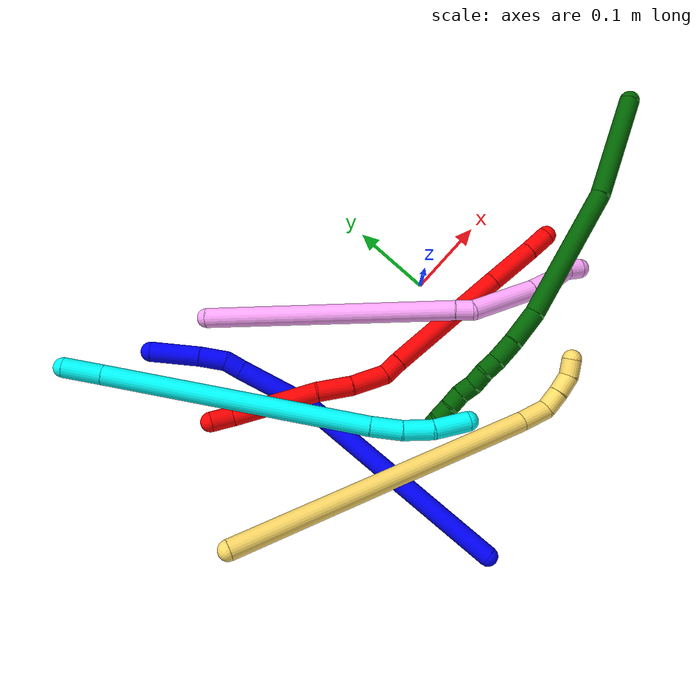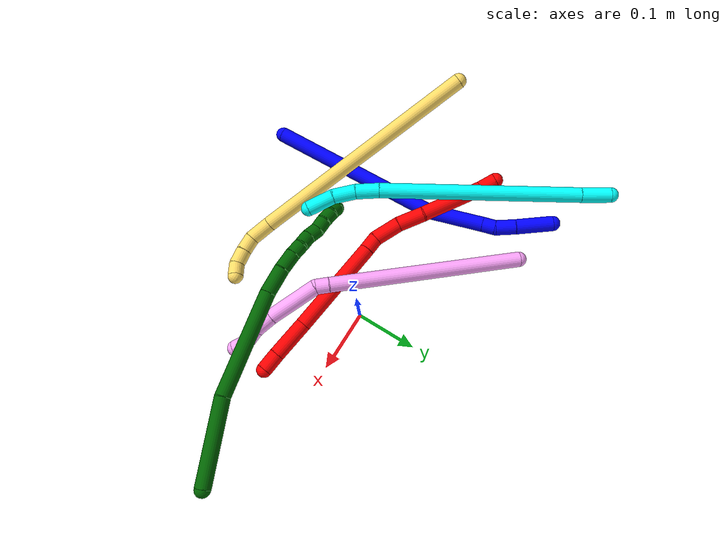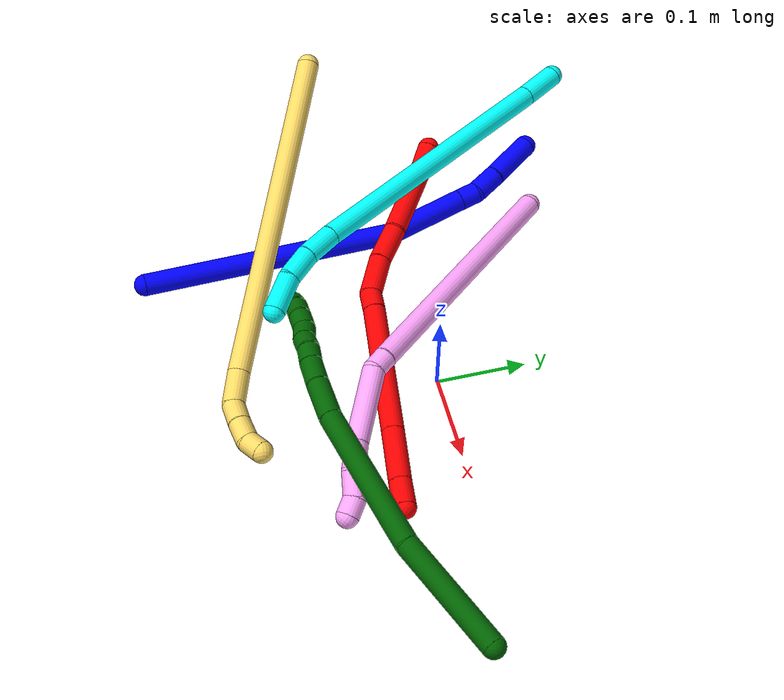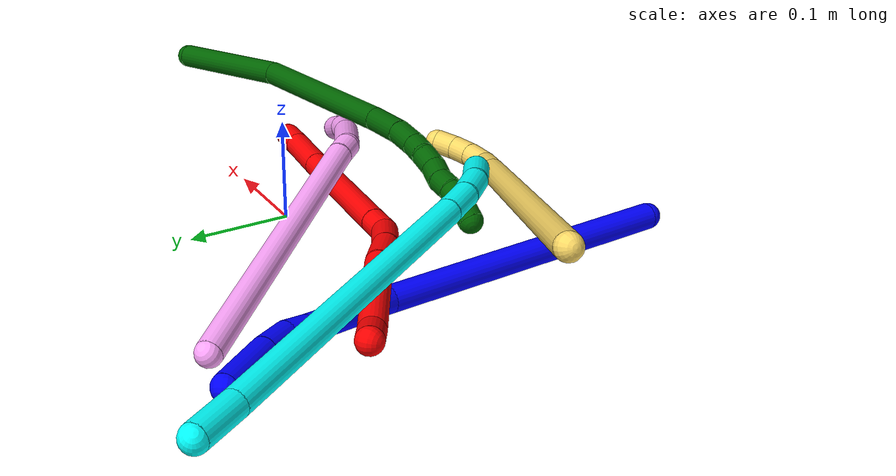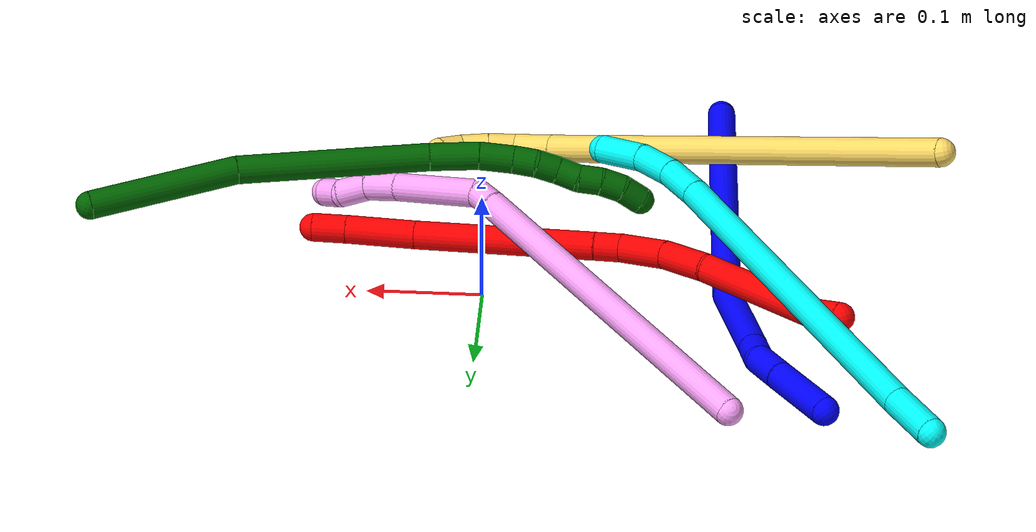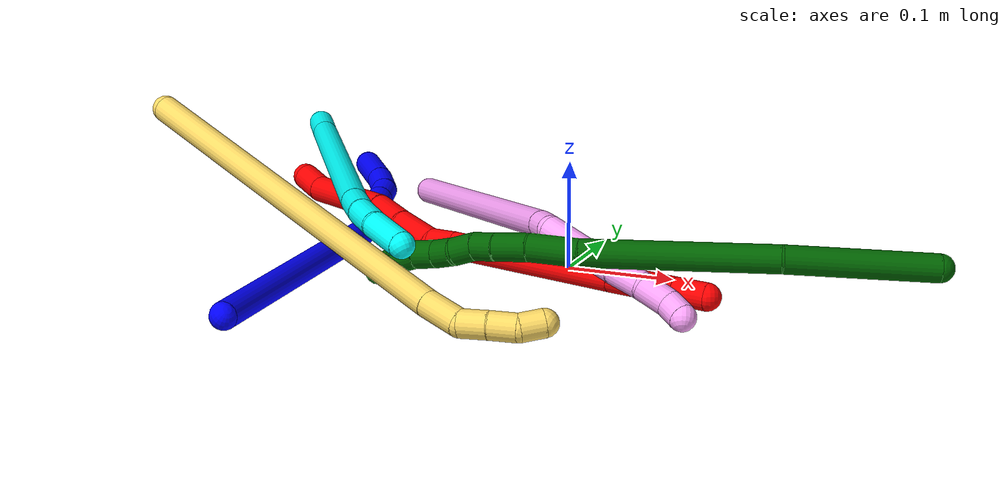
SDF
<sdf version="1.7">
 <world name="default">
  <plugin name="TubeGeneratorPlugin" filename="libtube_generator_plugin.so"/>
  <model name="photoneo_s_sensor">
   <static>1</static>
   <pose>0 0 2 1.57079 1.57079 3.14159</pose>
   <link name="link">
    <inertial><mass>0.1</mass></inertial>
    <sensor name="sensor" type="depth">
     <update_rate>30</update_rate>
     <camera>
      <horizontal_fov>1.22</horizontal_fov>
      <image><width>1920</width><height>1200</height><format>B8G8R8</format></image>
      <clip><near>0.1</near><far>4</far></clip>
      <depth_camera><output>points</output></depth_camera>
     </camera>
     <plugin name="camera_plugin" filename="libgazebo_ros_depth_camera.so">
      <baseline>0.2</baseline>
      <alwaysOn>1</alwaysOn>
      <updateRate>0.0</updateRate>
      <cameraName>camera_ir</cameraName>
      <imageTopicName>/camera/color/image_raw</imageTopicName>
      <cameraInfoTopicName>/camera/color/camera_info</cameraInfoTopicName>
      <depthImageTopicName>/camera/depth/image_raw</depthImageTopicName>
      <depthImageCameraInfoTopicName>/camera/depth/camera_info</depthImageCameraInfoTopicName>
      <pointCloudTopicName>/camera/depth/points</pointCloudTopicName>
      <frameName>fr_optical</frameName>
      <pointCloudCutoff>0.1</pointCloudCutoff>
      <pointCloudCutoffMax>2.0</pointCloudCutoffMax>
      <distortionK1>0</distortionK1>
      <distortionK2>0</distortionK2>
      <distortionK3>0</distortionK3>
      <distortionT1>0</distortionT1>
      <distortionT2>0</distortionT2>
      <CxPrime>0</CxPrime>
      <Cx>0</Cx>
      <Cy>0</Cy>
      <focalLength>0</focalLength>
      <hackBaseline>0</hackBaseline>
     </plugin>
    </sensor>
   </link>
  </model>
  <gravity>0 0 -9.8</gravity>
  <magnetic_field>6e-06 2.3e-05 -4.2e-05</magnetic_field>
  <atmosphere type="adiabatic"/>
  <physics name="default_physics" default="0" type="ode">
   <max_step_size>0.003</max_step_size>
   <real_time_factor>1</real_time_factor>
   <real_time_update_rate>1000</real_time_update_rate>
   <max_contacts>10000</max_contacts>
   <ode>
    <solver>
     <type>quick</type>
     <iters>100</iters>
     <sor>1.3</sor>
     <use_dynamic_moi_rescaling>0</use_dynamic_moi_rescaling>
    </solver>
    <constraints>
     <contact_max_correcting_vel>0</contact_max_correcting_vel>
     <contact_surface_layer>0.001</contact_surface_layer>
     <cfm>0</cfm>
     <erp>0.2</erp>
    </constraints>
   </ode>
  </physics>
  <scene><ambient>0.4 0.4 0.4 1</ambient><background>0.7 0.7 0.7 1</background><shadows>0</shadows></scene>
  <audio><device>default</device></audio>
  <spherical_coordinates>
   <surface_model>EARTH_WGS84</surface_model>
   <latitude_deg>0</latitude_deg>
   <longitude_deg>0</longitude_deg>
   <elevation>0</elevation>
   <heading_deg>0</heading_deg>
  </spherical_coordinates>
  <model name="bin">
   <static>1</static>
   <link name="bottom">
    <collision name="collision-bottom">
     <pose>0 0 -0.01 0 -0 0</pose>
     <geometry><box><size>0.8 0.6 0.02</size></box></geometry>
     <surface>
      <friction><ode><mu>100</mu><mu2>100</mu2></ode></friction>
      <contact><collide_bitmask>65535</collide_bitmask></contact>
     </surface>
    </collision>
   </link>
   <link name="west_wall">
    <collision name="collision-west_wall">
     <pose>-0.41 0 0.1 0 -0 0</pose>
     <geometry><box><size>0.02 0.6 0.2</size></box></geometry>
     <surface>
      <friction><ode><mu>100</mu><mu2>100</mu2></ode></friction>
      <contact><collide_bitmask>65535</collide_bitmask></contact>
     </surface>
    </collision>
   </link>
   <link name="east_wall">
    <collision name="collision-east_wall">
     <pose>0.41 0 0.1 0 -0 0</pose>
     <geometry><box><size>0.02 0.6 0.2</size></box></geometry>
     <surface>
      <friction><ode><mu>100</mu><mu2>100</mu2></ode></friction>
      <contact><collide_bitmask>65535</collide_bitmask></contact>
     </surface>
    </collision>
   </link>
   <link name="south_wall">
    <collision name="collision-south_wall">
     <pose>0 -0.31 0.1 0 -0 0</pose>
     <geometry><box><size>0.8 0.02 0.2</size></box></geometry>
     <surface>
      <friction><ode><mu>100</mu><mu2>100</mu2></ode></friction>
      <contact><collide_bitmask>65535</collide_bitmask></contact>
     </surface>
    </collision>
   </link>
   <link name="north_wall">
    <collision name="collision-north_wall">
     <pose>0 0.31 0.1 0 -0 0</pose>
     <geometry><box><size>0.8 0.02 0.2</size></box></geometry>
     <surface>
      <friction><ode><mu>100</mu><mu2>100</mu2></ode></friction>
      <contact><collide_bitmask>65535</collide_bitmask></contact>
     </surface>
    </collision>
   </link>
  </model>
  <model name="1">
   <static>0</static>
   <link name="1">
    <collision name="collision-cylinder-e_1_1_4">
     <pose>-0.050897 0.113767 0.074178 -0.993003 -0.358559 0.195737</pose>
     <geometry><cylinder><radius>0.0125</radius><length>0.290075</length></cylinder></geometry>
     <surface>
      <friction><ode><mu>1.16</mu><mu2>1.16</mu2><slip1>0</slip1><slip2>0</slip2></ode></friction>
      <contact><ode><kp>1e+06</kp><kd>1</kd><max_vel>0</max_vel><min_depth>0.001</min_depth></ode></contact>
     </surface>
    </collision>
    <visual name="visual-cylinder-e_1_1_4">
     <pose>-0.050897 0.113767 0.074178 -0.993003 -0.358559 0.195737</pose>
     <geometry><cylinder><radius>0.0125</radius><length>0.290075</length></cylinder></geometry>
     <material><ambient>0 0 1 1</ambient></material>
    </visual>
    <collision name="collision-cylinder-e_2_4_5">
     <pose>-0.107073 0.266599 0.173853 -0.992549 -0.112685 0.061062</pose>
     <geometry><cylinder><radius>0.0125</radius><length>0.093894</length></cylinder></geometry>
     <surface>
      <friction><ode><mu>1.16</mu><mu2>1.16</mu2><slip1>0</slip1><slip2>0</slip2></ode></friction>
      <contact><ode><kp>1e+06</kp><kd>1</kd><max_vel>0</max_vel><min_depth>0.001</min_depth></ode></contact>
     </surface>
    </collision>
    <visual name="visual-cylinder-e_2_4_5">
     <pose>-0.107073 0.266599 0.173853 -0.992549 -0.112685 0.061062</pose>
     <geometry><cylinder><radius>0.0125</radius><length>0.093894</length></cylinder></geometry>
     <material><ambient>0 0 1 1</ambient></material>
    </visual>
    <collision name="collision-cylinder-e_3_5_6">
     <pose>-0.113775 0.315081 0.20485 -1.04216 -0.129692 0.074513</pose>
     <geometry><cylinder><radius>0.0125</radius><length>0.021997</length></cylinder></geometry>
     <surface>
      <friction><ode><mu>1.16</mu><mu2>1.16</mu2><slip1>0</slip1><slip2>0</slip2></ode></friction>
      <contact><ode><kp>1e+06</kp><kd>1</kd><max_vel>0</max_vel><min_depth>0.001</min_depth></ode></contact>
     </surface>
    </collision>
    <visual name="visual-cylinder-e_3_5_6">
     <pose>-0.113775 0.315081 0.20485 -1.04216 -0.129692 0.074513</pose>
     <geometry><cylinder><radius>0.0125</radius><length>0.021997</length></cylinder></geometry>
     <material><ambient>0 0 1 1</ambient></material>
    </visual>
    <collision name="collision-cylinder-e_4_6_7">
     <pose>-0.112528 0.336599 0.22122 -0.838946 0.162667 -0.072668</pose>
     <geometry><cylinder><radius>0.0125</radius><length>0.032965</length></cylinder></geometry>
     <surface>
      <friction><ode><mu>1.16</mu><mu2>1.16</mu2><slip1>0</slip1><slip2>0</slip2></ode></friction>
      <contact><ode><kp>1e+06</kp><kd>1</kd><max_vel>0</max_vel><min_depth>0.001</min_depth></ode></contact>
     </surface>
    </collision>
    <visual name="visual-cylinder-e_4_6_7">
     <pose>-0.112528 0.336599 0.22122 -0.838946 0.162667 -0.072668</pose>
     <geometry><cylinder><radius>0.0125</radius><length>0.032965</length></cylinder></geometry>
     <material><ambient>0 0 1 1</ambient></material>
    </visual>
    <collision name="collision-cylinder-e_5_7_2">
     <pose>-0.103945 0.369138 0.25399 -0.750877 0.194888 -0.077018</pose>
     <geometry><cylinder><radius>0.0125</radius><length>0.061069</length></cylinder></geometry>
     <surface>
      <friction><ode><mu>1.16</mu><mu2>1.16</mu2><slip1>0</slip1><slip2>0</slip2></ode></friction>
      <contact><ode><kp>1e+06</kp><kd>1</kd><max_vel>0</max_vel><min_depth>0.001</min_depth></ode></contact>
     </surface>
    </collision>
    <visual name="visual-cylinder-e_5_7_2">
     <pose>-0.103945 0.369138 0.25399 -0.750877 0.194888 -0.077018</pose>
     <geometry><cylinder><radius>0.0125</radius><length>0.061069</length></cylinder></geometry>
     <material><ambient>0 0 1 1</ambient></material>
    </visual>
    <collision name="collision-sphere-2">
     <pose>-0.098032 0.389577 0.27589 0 -0 0</pose>
     <geometry><sphere><radius>0.0125</radius></sphere></geometry>
     <surface>
      <friction><ode><mu>1.16</mu><mu2>1.16</mu2><slip1>0</slip1><slip2>0</slip2></ode></friction>
      <contact><ode><kp>1e+06</kp><kd>1</kd><max_vel>0</max_vel><min_depth>0.001</min_depth></ode></contact>
     </surface>
    </collision>
    <visual name="visual-sphere-2">
     <pose>-0.098032 0.389577 0.27589 0 -0 0</pose>
     <geometry><sphere><radius>0.0125</radius></sphere></geometry>
     <material><ambient>0 0 1 1</ambient></material>
    </visual>
    <collision name="collision-sphere-7">
     <pose>-0.109859 0.348699 0.232089 0 -0 0</pose>
     <geometry><sphere><radius>0.0125</radius></sphere></geometry>
     <surface>
      <friction><ode><mu>1.16</mu><mu2>1.16</mu2><slip1>0</slip1><slip2>0</slip2></ode></friction>
      <contact><ode><kp>1e+06</kp><kd>1</kd><max_vel>0</max_vel><min_depth>0.001</min_depth></ode></contact>
     </surface>
    </collision>
    <visual name="visual-sphere-7">
     <pose>-0.109859 0.348699 0.232089 0 -0 0</pose>
     <geometry><sphere><radius>0.0125</radius></sphere></geometry>
     <material><ambient>0 0 1 1</ambient></material>
    </visual>
    <collision name="collision-sphere-6">
     <pose>-0.115197 0.324499 0.210351 0 -0 0</pose>
     <geometry><sphere><radius>0.0125</radius></sphere></geometry>
     <surface>
      <friction><ode><mu>1.16</mu><mu2>1.16</mu2><slip1>0</slip1><slip2>0</slip2></ode></friction>
      <contact><ode><kp>1e+06</kp><kd>1</kd><max_vel>0</max_vel><min_depth>0.001</min_depth></ode></contact>
     </surface>
    </collision>
    <visual name="visual-sphere-6">
     <pose>-0.115197 0.324499 0.210351 0 -0 0</pose>
     <geometry><sphere><radius>0.0125</radius></sphere></geometry>
     <material><ambient>0 0 1 1</ambient></material>
    </visual>
    <collision name="collision-sphere-5">
     <pose>-0.112352 0.305664 0.199349 0 -0 0</pose>
     <geometry><sphere><radius>0.0125</radius></sphere></geometry>
     <surface>
      <friction><ode><mu>1.16</mu><mu2>1.16</mu2><slip1>0</slip1><slip2>0</slip2></ode></friction>
      <contact><ode><kp>1e+06</kp><kd>1</kd><max_vel>0</max_vel><min_depth>0.001</min_depth></ode></contact>
     </surface>
    </collision>
    <visual name="visual-sphere-5">
     <pose>-0.112352 0.305664 0.199349 0 -0 0</pose>
     <geometry><sphere><radius>0.0125</radius></sphere></geometry>
     <material><ambient>0 0 1 1</ambient></material>
    </visual>
    <collision name="collision-sphere-1">
     <geometry><sphere><radius>0.0125</radius></sphere></geometry>
     <surface>
      <friction><ode><mu>1.16</mu><mu2>1.16</mu2><slip1>0</slip1><slip2>0</slip2></ode></friction>
      <contact><ode><kp>1e+06</kp><kd>1</kd><max_vel>0</max_vel><min_depth>0.001</min_depth></ode></contact>
     </surface>
    </collision>
    <visual name="visual-sphere-1">
     <geometry><sphere><radius>0.0125</radius></sphere></geometry>
     <material><ambient>0 0 1 1</ambient></material>
    </visual>
    <collision name="collision-sphere-4">
     <pose>-0.101794 0.227534 0.148356 0 -0 0</pose>
     <geometry><sphere><radius>0.0125</radius></sphere></geometry>
     <surface>
      <friction><ode><mu>1.16</mu><mu2>1.16</mu2><slip1>0</slip1><slip2>0</slip2></ode></friction>
      <contact><ode><kp>1e+06</kp><kd>1</kd><max_vel>0</max_vel><min_depth>0.001</min_depth></ode></contact>
     </surface>
    </collision>
    <visual name="visual-sphere-4">
     <pose>-0.101794 0.227534 0.148356 0 -0 0</pose>
     <geometry><sphere><radius>0.0125</radius></sphere></geometry>
     <material><ambient>0 0 1 1</ambient></material>
    </visual>
    <inertial>
     <pose>-0.074755 0.197206 0.130301 0 -0 0</pose>
     <mass>0.5</mass>
     <inertia>
      <ixx>0.002345</ixx>
      <ixy>0</ixy>
      <ixz>0</ixz>
      <iyy>0.001678</iyy>
      <iyz>0</iyz>
      <izz>-0.000941</izz>
     </inertia>
    </inertial>
   </link>
   <pose>-0.199715 -0.287975 0.015601 2.38694 -0.475471 -2.70435</pose>
  </model>
  <model name="2">
   <static>0</static>
   <link name="2">
    <collision name="collision-cylinder-e_1_1_4">
     <pose>0.012544 -0.002848 -0.00646 2.72633 1.05814 2.44991</pose>
     <geometry><cylinder><radius>0.0125</radius><length>0.028788</length></cylinder></geometry>
     <surface>
      <friction><ode><mu>1.16</mu><mu2>1.16</mu2><slip1>0</slip1><slip2>0</slip2></ode></friction>
      <contact><ode><kp>1e+06</kp><kd>1</kd><max_vel>0</max_vel><min_depth>0.001</min_depth></ode></contact>
     </surface>
    </collision>
    <visual name="visual-cylinder-e_1_1_4">
     <pose>0.012544 -0.002848 -0.00646 2.72633 1.05814 2.44991</pose>
     <geometry><cylinder><radius>0.0125</radius><length>0.028788</length></cylinder></geometry>
     <material><ambient>1 0 0 1</ambient></material>
    </visual>
    <collision name="collision-cylinder-e_2_4_5">
     <pose>0.072321 -0.000954 -0.037688 -2.95241 1.08042 -2.8278</pose>
     <geometry><cylinder><radius>0.0125</radius><length>0.107088</length></cylinder></geometry>
     <surface>
      <friction><ode><mu>1.16</mu><mu2>1.16</mu2><slip1>0</slip1><slip2>0</slip2></ode></friction>
      <contact><ode><kp>1e+06</kp><kd>1</kd><max_vel>0</max_vel><min_depth>0.001</min_depth></ode></contact>
     </surface>
    </collision>
    <visual name="visual-cylinder-e_2_4_5">
     <pose>0.072321 -0.000954 -0.037688 -2.95241 1.08042 -2.8278</pose>
     <geometry><cylinder><radius>0.0125</radius><length>0.107088</length></cylinder></geometry>
     <material><ambient>1 0 0 1</ambient></material>
    </visual>
    <collision name="collision-cylinder-e_3_5_6">
     <pose>0.139608 0.002159 -0.070816 2.94925 1.16909 2.85205</pose>
     <geometry><cylinder><radius>0.0125</radius><length>0.043573</length></cylinder></geometry>
     <surface>
      <friction><ode><mu>1.16</mu><mu2>1.16</mu2><slip1>0</slip1><slip2>0</slip2></ode></friction>
      <contact><ode><kp>1e+06</kp><kd>1</kd><max_vel>0</max_vel><min_depth>0.001</min_depth></ode></contact>
     </surface>
    </collision>
    <visual name="visual-cylinder-e_3_5_6">
     <pose>0.139608 0.002159 -0.070816 2.94925 1.16909 2.85205</pose>
     <geometry><cylinder><radius>0.0125</radius><length>0.043573</length></cylinder></geometry>
     <material><ambient>1 0 0 1</ambient></material>
    </visual>
    <collision name="collision-cylinder-e_4_6_7">
     <pose>0.178562 -0.002478 -0.090715 2.88648 1.00803 2.68463</pose>
     <geometry><cylinder><radius>0.0125</radius><length>0.044698</length></cylinder></geometry>
     <surface>
      <friction><ode><mu>1.16</mu><mu2>1.16</mu2><slip1>0</slip1><slip2>0</slip2></ode></friction>
      <contact><ode><kp>1e+06</kp><kd>1</kd><max_vel>0</max_vel><min_depth>0.001</min_depth></ode></contact>
     </surface>
    </collision>
    <visual name="visual-cylinder-e_4_6_7">
     <pose>0.178562 -0.002478 -0.090715 2.88648 1.00803 2.68463</pose>
     <geometry><cylinder><radius>0.0125</radius><length>0.044698</length></cylinder></geometry>
     <material><ambient>1 0 0 1</ambient></material>
    </visual>
    <collision name="collision-cylinder-e_5_7_8">
     <pose>0.204306 -0.005085 -0.112141 -3.10095 0.604921 -3.0115</pose>
     <geometry><cylinder><radius>0.0125</radius><length>0.024062</length></cylinder></geometry>
     <surface>
      <friction><ode><mu>1.16</mu><mu2>1.16</mu2><slip1>0</slip1><slip2>0</slip2></ode></friction>
      <contact><ode><kp>1e+06</kp><kd>1</kd><max_vel>0</max_vel><min_depth>0.001</min_depth></ode></contact>
     </surface>
    </collision>
    <visual name="visual-cylinder-e_5_7_8">
     <pose>0.204306 -0.005085 -0.112141 -3.10095 0.604921 -3.0115</pose>
     <geometry><cylinder><radius>0.0125</radius><length>0.024062</length></cylinder></geometry>
     <material><ambient>1 0 0 1</ambient></material>
    </visual>
    <collision name="collision-cylinder-e_6_8_9">
     <pose>0.259719 -0.005137 -0.185174 3.1344 0.655662 3.12046</pose>
     <geometry><cylinder><radius>0.0125</radius><length>0.159332</length></cylinder></geometry>
     <surface>
      <friction><ode><mu>1.16</mu><mu2>1.16</mu2><slip1>0</slip1><slip2>0</slip2></ode></friction>
      <contact><ode><kp>1e+06</kp><kd>1</kd><max_vel>0</max_vel><min_depth>0.001</min_depth></ode></contact>
     </surface>
    </collision>
    <visual name="visual-cylinder-e_6_8_9">
     <pose>0.259719 -0.005137 -0.185174 3.1344 0.655662 3.12046</pose>
     <geometry><cylinder><radius>0.0125</radius><length>0.159332</length></cylinder></geometry>
     <material><ambient>1 0 0 1</ambient></material>
    </visual>
    <collision name="collision-cylinder-e_7_9_10">
     <pose>0.327451 -0.00526 -0.272757 -3.12805 0.664902 -3.10238</pose>
     <geometry><cylinder><radius>0.0125</radius><length>0.062113</length></cylinder></geometry>
     <surface>
      <friction><ode><mu>1.16</mu><mu2>1.16</mu2><slip1>0</slip1><slip2>0</slip2></ode></friction>
      <contact><ode><kp>1e+06</kp><kd>1</kd><max_vel>0</max_vel><min_depth>0.001</min_depth></ode></contact>
     </surface>
    </collision>
    <visual name="visual-cylinder-e_7_9_10">
     <pose>0.327451 -0.00526 -0.272757 -3.12805 0.664902 -3.10238</pose>
     <geometry><cylinder><radius>0.0125</radius><length>0.062113</length></cylinder></geometry>
     <material><ambient>1 0 0 1</ambient></material>
    </visual>
    <collision name="collision-cylinder-e_8_10_2">
     <pose>0.355597 -0.004837 -0.309423 -3.13408 0.633642 -3.11866</pose>
     <geometry><cylinder><radius>0.0125</radius><length>0.030347</length></cylinder></geometry>
     <surface>
      <friction><ode><mu>1.16</mu><mu2>1.16</mu2><slip1>0</slip1><slip2>0</slip2></ode></friction>
      <contact><ode><kp>1e+06</kp><kd>1</kd><max_vel>0</max_vel><min_depth>0.001</min_depth></ode></contact>
     </surface>
    </collision>
    <visual name="visual-cylinder-e_8_10_2">
     <pose>0.355597 -0.004837 -0.309423 -3.13408 0.633642 -3.11866</pose>
     <geometry><cylinder><radius>0.0125</radius><length>0.030347</length></cylinder></geometry>
     <material><ambient>1 0 0 1</ambient></material>
    </visual>
    <collision name="collision-sphere-2">
     <pose>0.36458 -0.004745 -0.321651 0 -0 0</pose>
     <geometry><sphere><radius>0.0125</radius></sphere></geometry>
     <surface>
      <friction><ode><mu>1.16</mu><mu2>1.16</mu2><slip1>0</slip1><slip2>0</slip2></ode></friction>
      <contact><ode><kp>1e+06</kp><kd>1</kd><max_vel>0</max_vel><min_depth>0.001</min_depth></ode></contact>
     </surface>
    </collision>
    <visual name="visual-sphere-2">
     <pose>0.36458 -0.004745 -0.321651 0 -0 0</pose>
     <geometry><sphere><radius>0.0125</radius></sphere></geometry>
     <material><ambient>1 0 0 1</ambient></material>
    </visual>
    <collision name="collision-sphere-10">
     <pose>0.346613 -0.004929 -0.297196 0 -0 0</pose>
     <geometry><sphere><radius>0.0125</radius></sphere></geometry>
     <surface>
      <friction><ode><mu>1.16</mu><mu2>1.16</mu2><slip1>0</slip1><slip2>0</slip2></ode></friction>
      <contact><ode><kp>1e+06</kp><kd>1</kd><max_vel>0</max_vel><min_depth>0.001</min_depth></ode></contact>
     </surface>
    </collision>
    <visual name="visual-sphere-10">
     <pose>0.346613 -0.004929 -0.297196 0 -0 0</pose>
     <geometry><sphere><radius>0.0125</radius></sphere></geometry>
     <material><ambient>1 0 0 1</ambient></material>
    </visual>
    <collision name="collision-sphere-9">
     <pose>0.30829 -0.005591 -0.248319 0 -0 0</pose>
     <geometry><sphere><radius>0.0125</radius></sphere></geometry>
     <surface>
      <friction><ode><mu>1.16</mu><mu2>1.16</mu2><slip1>0</slip1><slip2>0</slip2></ode></friction>
      <contact><ode><kp>1e+06</kp><kd>1</kd><max_vel>0</max_vel><min_depth>0.001</min_depth></ode></contact>
     </surface>
    </collision>
    <visual name="visual-sphere-9">
     <pose>0.30829 -0.005591 -0.248319 0 -0 0</pose>
     <geometry><sphere><radius>0.0125</radius></sphere></geometry>
     <material><ambient>1 0 0 1</ambient></material>
    </visual>
    <collision name="collision-sphere-4">
     <pose>0.025087 -0.005697 -0.01292 0 -0 0</pose>
     <geometry><sphere><radius>0.0125</radius></sphere></geometry>
     <surface>
      <friction><ode><mu>1.16</mu><mu2>1.16</mu2><slip1>0</slip1><slip2>0</slip2></ode></friction>
      <contact><ode><kp>1e+06</kp><kd>1</kd><max_vel>0</max_vel><min_depth>0.001</min_depth></ode></contact>
     </surface>
    </collision>
    <visual name="visual-sphere-4">
     <pose>0.025087 -0.005697 -0.01292 0 -0 0</pose>
     <geometry><sphere><radius>0.0125</radius></sphere></geometry>
     <material><ambient>1 0 0 1</ambient></material>
    </visual>
    <collision name="collision-sphere-1">
     <geometry><sphere><radius>0.0125</radius></sphere></geometry>
     <surface>
      <friction><ode><mu>1.16</mu><mu2>1.16</mu2><slip1>0</slip1><slip2>0</slip2></ode></friction>
      <contact><ode><kp>1e+06</kp><kd>1</kd><max_vel>0</max_vel><min_depth>0.001</min_depth></ode></contact>
     </surface>
    </collision>
    <visual name="visual-sphere-1">
     <geometry><sphere><radius>0.0125</radius></sphere></geometry>
     <material><ambient>1 0 0 1</ambient></material>
    </visual>
    <collision name="collision-sphere-8">
     <pose>0.211148 -0.004683 -0.122029 0 -0 0</pose>
     <geometry><sphere><radius>0.0125</radius></sphere></geometry>
     <surface>
      <friction><ode><mu>1.16</mu><mu2>1.16</mu2><slip1>0</slip1><slip2>0</slip2></ode></friction>
      <contact><ode><kp>1e+06</kp><kd>1</kd><max_vel>0</max_vel><min_depth>0.001</min_depth></ode></contact>
     </surface>
    </collision>
    <visual name="visual-sphere-8">
     <pose>0.211148 -0.004683 -0.122029 0 -0 0</pose>
     <geometry><sphere><radius>0.0125</radius></sphere></geometry>
     <material><ambient>1 0 0 1</ambient></material>
    </visual>
    <collision name="collision-sphere-5">
     <pose>0.119555 0.003788 -0.062455 0 -0 0</pose>
     <geometry><sphere><radius>0.0125</radius></sphere></geometry>
     <surface>
      <friction><ode><mu>1.16</mu><mu2>1.16</mu2><slip1>0</slip1><slip2>0</slip2></ode></friction>
      <contact><ode><kp>1e+06</kp><kd>1</kd><max_vel>0</max_vel><min_depth>0.001</min_depth></ode></contact>
     </surface>
    </collision>
    <visual name="visual-sphere-5">
     <pose>0.119555 0.003788 -0.062455 0 -0 0</pose>
     <geometry><sphere><radius>0.0125</radius></sphere></geometry>
     <material><ambient>1 0 0 1</ambient></material>
    </visual>
    <collision name="collision-sphere-6">
     <pose>0.15966 0.000531 -0.079177 0 -0 0</pose>
     <geometry><sphere><radius>0.0125</radius></sphere></geometry>
     <surface>
      <friction><ode><mu>1.16</mu><mu2>1.16</mu2><slip1>0</slip1><slip2>0</slip2></ode></friction>
      <contact><ode><kp>1e+06</kp><kd>1</kd><max_vel>0</max_vel><min_depth>0.001</min_depth></ode></contact>
     </surface>
    </collision>
    <visual name="visual-sphere-6">
     <pose>0.15966 0.000531 -0.079177 0 -0 0</pose>
     <geometry><sphere><radius>0.0125</radius></sphere></geometry>
     <material><ambient>1 0 0 1</ambient></material>
    </visual>
    <collision name="collision-sphere-7">
     <pose>0.197464 -0.005487 -0.102253 0 -0 0</pose>
     <geometry><sphere><radius>0.0125</radius></sphere></geometry>
     <surface>
      <friction><ode><mu>1.16</mu><mu2>1.16</mu2><slip1>0</slip1><slip2>0</slip2></ode></friction>
      <contact><ode><kp>1e+06</kp><kd>1</kd><max_vel>0</max_vel><min_depth>0.001</min_depth></ode></contact>
     </surface>
    </collision>
    <visual name="visual-sphere-7">
     <pose>0.197464 -0.005487 -0.102253 0 -0 0</pose>
     <geometry><sphere><radius>0.0125</radius></sphere></geometry>
     <material><ambient>1 0 0 1</ambient></material>
    </visual>
    <inertial>
     <pose>0.199196 -0.00323 -0.139793 0 -0 0</pose>
     <mass>0.5</mass>
     <inertia>
      <ixx>-0.000329</ixx>
      <ixy>0</ixy>
      <ixz>0</ixz>
      <iyy>0.000489</iyy>
      <iyz>0</iyz>
      <izz>-0.000369</izz>
     </inertia>
    </inertial>
   </link>
   <pose>-0.306338 0.072873 0.041681 1.5495 0.048228 -1.03977</pose>
  </model>
  <model name="3">
   <static>0</static>
   <link name="3">
    <collision name="collision-cylinder-e_1_1_4">
     <pose>0.000604 -0.020691 -0.012845 2.12636 0.024788 0.044559</pose>
     <geometry><cylinder><radius>0.0125</radius><length>0.048723</length></cylinder></geometry>
     <surface>
      <friction><ode><mu>1.16</mu><mu2>1.16</mu2><slip1>0</slip1><slip2>0</slip2></ode></friction>
      <contact><ode><kp>1e+06</kp><kd>1</kd><max_vel>0</max_vel><min_depth>0.001</min_depth></ode></contact>
     </surface>
    </collision>
    <visual name="visual-cylinder-e_1_1_4">
     <pose>0.000604 -0.020691 -0.012845 2.12636 0.024788 0.044559</pose>
     <geometry><cylinder><radius>0.0125</radius><length>0.048723</length></cylinder></geometry>
     <material><ambient>0.003922 1 0.996078 1</ambient></material>
    </visual>
    <collision name="collision-cylinder-e_2_4_5">
     <pose>0.007344 -0.185318 -0.106884 2.0844 0.037117 0.063539</pose>
     <geometry><cylinder><radius>0.0125</radius><length>0.330743</length></cylinder></geometry>
     <surface>
      <friction><ode><mu>1.16</mu><mu2>1.16</mu2><slip1>0</slip1><slip2>0</slip2></ode></friction>
      <contact><ode><kp>1e+06</kp><kd>1</kd><max_vel>0</max_vel><min_depth>0.001</min_depth></ode></contact>
     </surface>
    </collision>
    <visual name="visual-cylinder-e_2_4_5">
     <pose>0.007344 -0.185318 -0.106884 2.0844 0.037117 0.063539</pose>
     <geometry><cylinder><radius>0.0125</radius><length>0.330743</length></cylinder></geometry>
     <material><ambient>0.003922 1 0.996078 1</ambient></material>
    </visual>
    <collision name="collision-cylinder-e_3_5_6">
     <pose>0.015118 -0.345528 -0.198484 2.13971 0.084521 0.154156</pose>
     <geometry><cylinder><radius>0.0125</radius><length>0.03877</length></cylinder></geometry>
     <surface>
      <friction><ode><mu>1.16</mu><mu2>1.16</mu2><slip1>0</slip1><slip2>0</slip2></ode></friction>
      <contact><ode><kp>1e+06</kp><kd>1</kd><max_vel>0</max_vel><min_depth>0.001</min_depth></ode></contact>
     </surface>
    </collision>
    <visual name="visual-cylinder-e_3_5_6">
     <pose>0.015118 -0.345528 -0.198484 2.13971 0.084521 0.154156</pose>
     <geometry><cylinder><radius>0.0125</radius><length>0.03877</length></cylinder></geometry>
     <material><ambient>0.003922 1 0.996078 1</ambient></material>
    </visual>
    <collision name="collision-cylinder-e_4_6_7">
     <pose>0.020365 -0.375713 -0.220491 2.26586 0.19674 0.415502</pose>
     <geometry><cylinder><radius>0.0125</radius><length>0.036943</length></cylinder></geometry>
     <surface>
      <friction><ode><mu>1.16</mu><mu2>1.16</mu2><slip1>0</slip1><slip2>0</slip2></ode></friction>
      <contact><ode><kp>1e+06</kp><kd>1</kd><max_vel>0</max_vel><min_depth>0.001</min_depth></ode></contact>
     </surface>
    </collision>
    <visual name="visual-cylinder-e_4_6_7">
     <pose>0.020365 -0.375713 -0.220491 2.26586 0.19674 0.415502</pose>
     <geometry><cylinder><radius>0.0125</radius><length>0.036943</length></cylinder></geometry>
     <material><ambient>0.003922 1 0.996078 1</ambient></material>
    </visual>
    <collision name="collision-cylinder-e_5_7_2">
     <pose>0.031055 -0.402812 -0.248773 2.47268 0.321411 0.872924</pose>
     <geometry><cylinder><radius>0.0125</radius><length>0.044821</length></cylinder></geometry>
     <surface>
      <friction><ode><mu>1.16</mu><mu2>1.16</mu2><slip1>0</slip1><slip2>0</slip2></ode></friction>
      <contact><ode><kp>1e+06</kp><kd>1</kd><max_vel>0</max_vel><min_depth>0.001</min_depth></ode></contact>
     </surface>
    </collision>
    <visual name="visual-cylinder-e_5_7_2">
     <pose>0.031055 -0.402812 -0.248773 2.47268 0.321411 0.872924</pose>
     <geometry><cylinder><radius>0.0125</radius><length>0.044821</length></cylinder></geometry>
     <material><ambient>0.003922 1 0.996078 1</ambient></material>
    </visual>
    <collision name="collision-sphere-2">
     <pose>0.038135 -0.415998 -0.265454 0 -0 0</pose>
     <geometry><sphere><radius>0.0125</radius></sphere></geometry>
     <surface>
      <friction><ode><mu>1.16</mu><mu2>1.16</mu2><slip1>0</slip1><slip2>0</slip2></ode></friction>
      <contact><ode><kp>1e+06</kp><kd>1</kd><max_vel>0</max_vel><min_depth>0.001</min_depth></ode></contact>
     </surface>
    </collision>
    <visual name="visual-sphere-2">
     <pose>0.038135 -0.415998 -0.265454 0 -0 0</pose>
     <geometry><sphere><radius>0.0125</radius></sphere></geometry>
     <material><ambient>0.003922 1 0.996078 1</ambient></material>
    </visual>
    <collision name="collision-sphere-7">
     <pose>0.023975 -0.389626 -0.232093 0 -0 0</pose>
     <geometry><sphere><radius>0.0125</radius></sphere></geometry>
     <surface>
      <friction><ode><mu>1.16</mu><mu2>1.16</mu2><slip1>0</slip1><slip2>0</slip2></ode></friction>
      <contact><ode><kp>1e+06</kp><kd>1</kd><max_vel>0</max_vel><min_depth>0.001</min_depth></ode></contact>
     </surface>
    </collision>
    <visual name="visual-sphere-7">
     <pose>0.023975 -0.389626 -0.232093 0 -0 0</pose>
     <geometry><sphere><radius>0.0125</radius></sphere></geometry>
     <material><ambient>0.003922 1 0.996078 1</ambient></material>
    </visual>
    <collision name="collision-sphere-6">
     <pose>0.016754 -0.361801 -0.20889 0 -0 0</pose>
     <geometry><sphere><radius>0.0125</radius></sphere></geometry>
     <surface>
      <friction><ode><mu>1.16</mu><mu2>1.16</mu2><slip1>0</slip1><slip2>0</slip2></ode></friction>
      <contact><ode><kp>1e+06</kp><kd>1</kd><max_vel>0</max_vel><min_depth>0.001</min_depth></ode></contact>
     </surface>
    </collision>
    <visual name="visual-sphere-6">
     <pose>0.016754 -0.361801 -0.20889 0 -0 0</pose>
     <geometry><sphere><radius>0.0125</radius></sphere></geometry>
     <material><ambient>0.003922 1 0.996078 1</ambient></material>
    </visual>
    <collision name="collision-sphere-5">
     <pose>0.013481 -0.329255 -0.188078 0 -0 0</pose>
     <geometry><sphere><radius>0.0125</radius></sphere></geometry>
     <surface>
      <friction><ode><mu>1.16</mu><mu2>1.16</mu2><slip1>0</slip1><slip2>0</slip2></ode></friction>
      <contact><ode><kp>1e+06</kp><kd>1</kd><max_vel>0</max_vel><min_depth>0.001</min_depth></ode></contact>
     </surface>
    </collision>
    <visual name="visual-sphere-5">
     <pose>0.013481 -0.329255 -0.188078 0 -0 0</pose>
     <geometry><sphere><radius>0.0125</radius></sphere></geometry>
     <material><ambient>0.003922 1 0.996078 1</ambient></material>
    </visual>
    <collision name="collision-sphere-1">
     <geometry><sphere><radius>0.0125</radius></sphere></geometry>
     <surface>
      <friction><ode><mu>1.16</mu><mu2>1.16</mu2><slip1>0</slip1><slip2>0</slip2></ode></friction>
      <contact><ode><kp>1e+06</kp><kd>1</kd><max_vel>0</max_vel><min_depth>0.001</min_depth></ode></contact>
     </surface>
    </collision>
    <visual name="visual-sphere-1">
     <geometry><sphere><radius>0.0125</radius></sphere></geometry>
     <material><ambient>0.003922 1 0.996078 1</ambient></material>
    </visual>
    <collision name="collision-sphere-4">
     <pose>0.001208 -0.041382 -0.02569 0 -0 0</pose>
     <geometry><sphere><radius>0.0125</radius></sphere></geometry>
     <surface>
      <friction><ode><mu>1.16</mu><mu2>1.16</mu2><slip1>0</slip1><slip2>0</slip2></ode></friction>
      <contact><ode><kp>1e+06</kp><kd>1</kd><max_vel>0</max_vel><min_depth>0.001</min_depth></ode></contact>
     </surface>
    </collision>
    <visual name="visual-sphere-4">
     <pose>0.001208 -0.041382 -0.02569 0 -0 0</pose>
     <geometry><sphere><radius>0.0125</radius></sphere></geometry>
     <material><ambient>0.003922 1 0.996078 1</ambient></material>
    </visual>
    <inertial>
     <pose>0.010378 -0.215263 -0.125936 0 -0 0</pose>
     <mass>0.5</mass>
     <inertia>
      <ixx>0.003254</ixx>
      <ixy>0</ixy>
      <ixz>0</ixz>
      <iyy>-0.001324</iyy>
      <iyz>0</iyz>
      <izz>0.002522</izz>
     </inertia>
    </inertial>
   </link>
   <pose>-0.377111 0.248401 0.054455 -0.53008 -0.441548 0.517663</pose>
  </model>
  <model name="4">
   <static>0</static>
   <link name="4">
    <collision name="collision-cylinder-e_1_1_4">
     <pose>0.028667 -0.13413 -0.077377 2.09404 0.183058 0.31519</pose>
     <geometry><cylinder><radius>0.0125</radius><length>0.314959</length></cylinder></geometry>
     <surface>
      <friction><ode><mu>1.16</mu><mu2>1.16</mu2><slip1>0</slip1><slip2>0</slip2></ode></friction>
      <contact><ode><kp>1e+06</kp><kd>1</kd><max_vel>0</max_vel><min_depth>0.001</min_depth></ode></contact>
     </surface>
    </collision>
    <visual name="visual-cylinder-e_1_1_4">
     <pose>0.028667 -0.13413 -0.077377 2.09404 0.183058 0.31519</pose>
     <geometry><cylinder><radius>0.0125</radius><length>0.314959</length></cylinder></geometry>
     <material><ambient>1 0.65098 0.996078 1</ambient></material>
    </visual>
    <collision name="collision-cylinder-e_2_4_5">
     <pose>0.059255 -0.276768 -0.160794 2.18813 0.182062 0.349881</pose>
     <geometry><cylinder><radius>0.0125</radius><length>0.021219</length></cylinder></geometry>
     <surface>
      <friction><ode><mu>1.16</mu><mu2>1.16</mu2><slip1>0</slip1><slip2>0</slip2></ode></friction>
      <contact><ode><kp>1e+06</kp><kd>1</kd><max_vel>0</max_vel><min_depth>0.001</min_depth></ode></contact>
     </surface>
    </collision>
    <visual name="visual-cylinder-e_2_4_5">
     <pose>0.059255 -0.276768 -0.160794 2.18813 0.182062 0.349881</pose>
     <geometry><cylinder><radius>0.0125</radius><length>0.021219</length></cylinder></geometry>
     <material><ambient>1 0.65098 0.996078 1</ambient></material>
    </visual>
    <collision name="collision-cylinder-e_3_5_6">
     <pose>0.084574 -0.307507 -0.193688 2.45011 0.591117 1.40348</pose>
     <geometry><cylinder><radius>0.0125</radius><length>0.083972</length></cylinder></geometry>
     <surface>
      <friction><ode><mu>1.16</mu><mu2>1.16</mu2><slip1>0</slip1><slip2>0</slip2></ode></friction>
      <contact><ode><kp>1e+06</kp><kd>1</kd><max_vel>0</max_vel><min_depth>0.001</min_depth></ode></contact>
     </surface>
    </collision>
    <visual name="visual-cylinder-e_3_5_6">
     <pose>0.084574 -0.307507 -0.193688 2.45011 0.591117 1.40348</pose>
     <geometry><cylinder><radius>0.0125</radius><length>0.083972</length></cylinder></geometry>
     <material><ambient>1 0.65098 0.996078 1</ambient></material>
    </visual>
    <collision name="collision-cylinder-e_4_6_7">
     <pose>0.117887 -0.337487 -0.229671 2.43771 0.691534 1.55157</pose>
     <geometry><cylinder><radius>0.0125</radius><length>0.031092</length></cylinder></geometry>
     <surface>
      <friction><ode><mu>1.16</mu><mu2>1.16</mu2><slip1>0</slip1><slip2>0</slip2></ode></friction>
      <contact><ode><kp>1e+06</kp><kd>1</kd><max_vel>0</max_vel><min_depth>0.001</min_depth></ode></contact>
     </surface>
    </collision>
    <visual name="visual-cylinder-e_4_6_7">
     <pose>0.117887 -0.337487 -0.229671 2.43771 0.691534 1.55157</pose>
     <geometry><cylinder><radius>0.0125</radius><length>0.031092</length></cylinder></geometry>
     <material><ambient>1 0.65098 0.996078 1</ambient></material>
    </visual>
    <collision name="collision-cylinder-e_5_7_8">
     <pose>0.138385 -0.348989 -0.247236 2.72317 0.853489 2.26786</pose>
     <geometry><cylinder><radius>0.0125</radius><length>0.028091</length></cylinder></geometry>
     <surface>
      <friction><ode><mu>1.16</mu><mu2>1.16</mu2><slip1>0</slip1><slip2>0</slip2></ode></friction>
      <contact><ode><kp>1e+06</kp><kd>1</kd><max_vel>0</max_vel><min_depth>0.001</min_depth></ode></contact>
     </surface>
    </collision>
    <visual name="visual-cylinder-e_5_7_8">
     <pose>0.138385 -0.348989 -0.247236 2.72317 0.853489 2.26786</pose>
     <geometry><cylinder><radius>0.0125</radius><length>0.028091</length></cylinder></geometry>
     <material><ambient>1 0.65098 0.996078 1</ambient></material>
    </visual>
    <collision name="collision-cylinder-e_6_8_2">
     <pose>0.153206 -0.357784 -0.263634 2.57694 0.422494 1.2732</pose>
     <geometry><cylinder><radius>0.0125</radius><length>0.020667</length></cylinder></geometry>
     <surface>
      <friction><ode><mu>1.16</mu><mu2>1.16</mu2><slip1>0</slip1><slip2>0</slip2></ode></friction>
      <contact><ode><kp>1e+06</kp><kd>1</kd><max_vel>0</max_vel><min_depth>0.001</min_depth></ode></contact>
     </surface>
    </collision>
    <visual name="visual-cylinder-e_6_8_2">
     <pose>0.153206 -0.357784 -0.263634 2.57694 0.422494 1.2732</pose>
     <geometry><cylinder><radius>0.0125</radius><length>0.020667</length></cylinder></geometry>
     <material><ambient>1 0.65098 0.996078 1</ambient></material>
    </visual>
    <collision name="collision-sphere-2">
     <pose>0.157444 -0.362827 -0.271596 0 -0 0</pose>
     <geometry><sphere><radius>0.0125</radius></sphere></geometry>
     <surface>
      <friction><ode><mu>1.16</mu><mu2>1.16</mu2><slip1>0</slip1><slip2>0</slip2></ode></friction>
      <contact><ode><kp>1e+06</kp><kd>1</kd><max_vel>0</max_vel><min_depth>0.001</min_depth></ode></contact>
     </surface>
    </collision>
    <visual name="visual-sphere-2">
     <pose>0.157444 -0.362827 -0.271596 0 -0 0</pose>
     <geometry><sphere><radius>0.0125</radius></sphere></geometry>
     <material><ambient>1 0.65098 0.996078 1</ambient></material>
    </visual>
    <collision name="collision-sphere-4">
     <pose>0.057334 -0.26826 -0.154754 0 -0 0</pose>
     <geometry><sphere><radius>0.0125</radius></sphere></geometry>
     <surface>
      <friction><ode><mu>1.16</mu><mu2>1.16</mu2><slip1>0</slip1><slip2>0</slip2></ode></friction>
      <contact><ode><kp>1e+06</kp><kd>1</kd><max_vel>0</max_vel><min_depth>0.001</min_depth></ode></contact>
     </surface>
    </collision>
    <visual name="visual-sphere-4">
     <pose>0.057334 -0.26826 -0.154754 0 -0 0</pose>
     <geometry><sphere><radius>0.0125</radius></sphere></geometry>
     <material><ambient>1 0.65098 0.996078 1</ambient></material>
    </visual>
    <collision name="collision-sphere-1">
     <geometry><sphere><radius>0.0125</radius></sphere></geometry>
     <surface>
      <friction><ode><mu>1.16</mu><mu2>1.16</mu2><slip1>0</slip1><slip2>0</slip2></ode></friction>
      <contact><ode><kp>1e+06</kp><kd>1</kd><max_vel>0</max_vel><min_depth>0.001</min_depth></ode></contact>
     </surface>
    </collision>
    <visual name="visual-sphere-1">
     <geometry><sphere><radius>0.0125</radius></sphere></geometry>
     <material><ambient>1 0.65098 0.996078 1</ambient></material>
    </visual>
    <collision name="collision-sphere-8">
     <pose>0.148969 -0.35274 -0.255672 0 -0 0</pose>
     <geometry><sphere><radius>0.0125</radius></sphere></geometry>
     <surface>
      <friction><ode><mu>1.16</mu><mu2>1.16</mu2><slip1>0</slip1><slip2>0</slip2></ode></friction>
      <contact><ode><kp>1e+06</kp><kd>1</kd><max_vel>0</max_vel><min_depth>0.001</min_depth></ode></contact>
     </surface>
    </collision>
    <visual name="visual-sphere-8">
     <pose>0.148969 -0.35274 -0.255672 0 -0 0</pose>
     <geometry><sphere><radius>0.0125</radius></sphere></geometry>
     <material><ambient>1 0.65098 0.996078 1</ambient></material>
    </visual>
    <collision name="collision-sphere-5">
     <pose>0.061176 -0.285276 -0.166834 0 -0 0</pose>
     <geometry><sphere><radius>0.0125</radius></sphere></geometry>
     <surface>
      <friction><ode><mu>1.16</mu><mu2>1.16</mu2><slip1>0</slip1><slip2>0</slip2></ode></friction>
      <contact><ode><kp>1e+06</kp><kd>1</kd><max_vel>0</max_vel><min_depth>0.001</min_depth></ode></contact>
     </surface>
    </collision>
    <visual name="visual-sphere-5">
     <pose>0.061176 -0.285276 -0.166834 0 -0 0</pose>
     <geometry><sphere><radius>0.0125</radius></sphere></geometry>
     <material><ambient>1 0.65098 0.996078 1</ambient></material>
    </visual>
    <collision name="collision-sphere-6">
     <pose>0.107973 -0.329738 -0.220542 0 -0 0</pose>
     <geometry><sphere><radius>0.0125</radius></sphere></geometry>
     <surface>
      <friction><ode><mu>1.16</mu><mu2>1.16</mu2><slip1>0</slip1><slip2>0</slip2></ode></friction>
      <contact><ode><kp>1e+06</kp><kd>1</kd><max_vel>0</max_vel><min_depth>0.001</min_depth></ode></contact>
     </surface>
    </collision>
    <visual name="visual-sphere-6">
     <pose>0.107973 -0.329738 -0.220542 0 -0 0</pose>
     <geometry><sphere><radius>0.0125</radius></sphere></geometry>
     <material><ambient>1 0.65098 0.996078 1</ambient></material>
    </visual>
    <collision name="collision-sphere-7">
     <pose>0.127801 -0.345237 -0.238799 0 -0 0</pose>
     <geometry><sphere><radius>0.0125</radius></sphere></geometry>
     <surface>
      <friction><ode><mu>1.16</mu><mu2>1.16</mu2><slip1>0</slip1><slip2>0</slip2></ode></friction>
      <contact><ode><kp>1e+06</kp><kd>1</kd><max_vel>0</max_vel><min_depth>0.001</min_depth></ode></contact>
     </surface>
    </collision>
    <visual name="visual-sphere-7">
     <pose>0.127801 -0.345237 -0.238799 0 -0 0</pose>
     <geometry><sphere><radius>0.0125</radius></sphere></geometry>
     <material><ambient>1 0.65098 0.996078 1</ambient></material>
    </visual>
    <inertial>
     <pose>0.056214 -0.203262 -0.127163 0 -0 0</pose>
     <mass>0.5</mass>
     <inertia>
      <ixx>0.003313</ixx>
      <ixy>0</ixy>
      <ixz>0</ixz>
      <iyy>-0.000282</iyy>
      <iyz>0</iyz>
      <izz>0.001728</izz>
     </inertia>
    </inertial>
   </link>
   <pose>-0.215872 0.172015 0.012223 -0.697027 0.159947 0.531676</pose>
  </model>
  <model name="5">
   <static>0</static>
   <link name="5">
    <collision name="collision-cylinder-e_1_1_4">
     <pose>0.022837 -0.064173 0.1824 0.3383 0.117563 0.0201</pose>
     <geometry><cylinder><radius>0.0125</radius><length>0.389408</length></cylinder></geometry>
     <surface>
      <friction><ode><mu>1.16</mu><mu2>1.16</mu2><slip1>0</slip1><slip2>0</slip2></ode></friction>
      <contact><ode><kp>1e+06</kp><kd>1</kd><max_vel>0</max_vel><min_depth>0.001</min_depth></ode></contact>
     </surface>
    </collision>
    <visual name="visual-cylinder-e_1_1_4">
     <pose>0.022837 -0.064173 0.1824 0.3383 0.117563 0.0201</pose>
     <geometry><cylinder><radius>0.0125</radius><length>0.389408</length></cylinder></geometry>
     <material><ambient>1 0.858824 0.4 1</ambient></material>
    </visual>
    <collision name="collision-cylinder-e_2_4_5">
     <pose>0.046687 -0.134109 0.38289 0.30841 0.053281 0.008284</pose>
     <geometry><cylinder><radius>0.0125</radius><length>0.038025</length></cylinder></geometry>
     <surface>
      <friction><ode><mu>1.16</mu><mu2>1.16</mu2><slip1>0</slip1><slip2>0</slip2></ode></friction>
      <contact><ode><kp>1e+06</kp><kd>1</kd><max_vel>0</max_vel><min_depth>0.001</min_depth></ode></contact>
     </surface>
    </collision>
    <visual name="visual-cylinder-e_2_4_5">
     <pose>0.046687 -0.134109 0.38289 0.30841 0.053281 0.008284</pose>
     <geometry><cylinder><radius>0.0125</radius><length>0.038025</length></cylinder></geometry>
     <material><ambient>1 0.858824 0.4 1</ambient></material>
    </visual>
    <collision name="collision-cylinder-e_3_5_6">
     <pose>0.043092 -0.139918 0.412896 0.003855 -0.368922 -0.000719</pose>
     <geometry><cylinder><radius>0.0125</radius><length>0.025552</length></cylinder></geometry>
     <surface>
      <friction><ode><mu>1.16</mu><mu2>1.16</mu2><slip1>0</slip1><slip2>0</slip2></ode></friction>
      <contact><ode><kp>1e+06</kp><kd>1</kd><max_vel>0</max_vel><min_depth>0.001</min_depth></ode></contact>
     </surface>
    </collision>
    <visual name="visual-cylinder-e_3_5_6">
     <pose>0.043092 -0.139918 0.412896 0.003855 -0.368922 -0.000719</pose>
     <geometry><cylinder><radius>0.0125</radius><length>0.025552</length></cylinder></geometry>
     <material><ambient>1 0.858824 0.4 1</ambient></material>
    </visual>
    <collision name="collision-cylinder-e_4_6_7">
     <pose>0.034249 -0.138844 0.436567 -0.095005 -0.34448 0.016539</pose>
     <geometry><cylinder><radius>0.0125</radius><length>0.02509</length></cylinder></geometry>
     <surface>
      <friction><ode><mu>1.16</mu><mu2>1.16</mu2><slip1>0</slip1><slip2>0</slip2></ode></friction>
      <contact><ode><kp>1e+06</kp><kd>1</kd><max_vel>0</max_vel><min_depth>0.001</min_depth></ode></contact>
     </surface>
    </collision>
    <visual name="visual-cylinder-e_4_6_7">
     <pose>0.034249 -0.138844 0.436567 -0.095005 -0.34448 0.016539</pose>
     <geometry><cylinder><radius>0.0125</radius><length>0.02509</length></cylinder></geometry>
     <material><ambient>1 0.858824 0.4 1</ambient></material>
    </visual>
    <collision name="collision-cylinder-e_5_7_2">
     <pose>0.023787 -0.133454 0.456272 -0.492772 -0.603856 0.156338</pose>
     <geometry><cylinder><radius>0.0125</radius><length>0.021926</length></cylinder></geometry>
     <surface>
      <friction><ode><mu>1.16</mu><mu2>1.16</mu2><slip1>0</slip1><slip2>0</slip2></ode></friction>
      <contact><ode><kp>1e+06</kp><kd>1</kd><max_vel>0</max_vel><min_depth>0.001</min_depth></ode></contact>
     </surface>
    </collision>
    <visual name="visual-cylinder-e_5_7_2">
     <pose>0.023787 -0.133454 0.456272 -0.492772 -0.603856 0.156338</pose>
     <geometry><cylinder><radius>0.0125</radius><length>0.021926</length></cylinder></geometry>
     <material><ambient>1 0.858824 0.4 1</ambient></material>
    </visual>
    <collision name="collision-sphere-2">
     <pose>0.017562 -0.129185 0.464223 0 -0 0</pose>
     <geometry><sphere><radius>0.0125</radius></sphere></geometry>
     <surface>
      <friction><ode><mu>1.16</mu><mu2>1.16</mu2><slip1>0</slip1><slip2>0</slip2></ode></friction>
      <contact><ode><kp>1e+06</kp><kd>1</kd><max_vel>0</max_vel><min_depth>0.001</min_depth></ode></contact>
     </surface>
    </collision>
    <visual name="visual-sphere-2">
     <pose>0.017562 -0.129185 0.464223 0 -0 0</pose>
     <geometry><sphere><radius>0.0125</radius></sphere></geometry>
     <material><ambient>1 0.858824 0.4 1</ambient></material>
    </visual>
    <collision name="collision-sphere-7">
     <pose>0.030012 -0.137724 0.448322 0 -0 0</pose>
     <geometry><sphere><radius>0.0125</radius></sphere></geometry>
     <surface>
      <friction><ode><mu>1.16</mu><mu2>1.16</mu2><slip1>0</slip1><slip2>0</slip2></ode></friction>
      <contact><ode><kp>1e+06</kp><kd>1</kd><max_vel>0</max_vel><min_depth>0.001</min_depth></ode></contact>
     </surface>
    </collision>
    <visual name="visual-sphere-7">
     <pose>0.030012 -0.137724 0.448322 0 -0 0</pose>
     <geometry><sphere><radius>0.0125</radius></sphere></geometry>
     <material><ambient>1 0.858824 0.4 1</ambient></material>
    </visual>
    <collision name="collision-sphere-6">
     <pose>0.038485 -0.139964 0.424813 0 -0 0</pose>
     <geometry><sphere><radius>0.0125</radius></sphere></geometry>
     <surface>
      <friction><ode><mu>1.16</mu><mu2>1.16</mu2><slip1>0</slip1><slip2>0</slip2></ode></friction>
      <contact><ode><kp>1e+06</kp><kd>1</kd><max_vel>0</max_vel><min_depth>0.001</min_depth></ode></contact>
     </surface>
    </collision>
    <visual name="visual-sphere-6">
     <pose>0.038485 -0.139964 0.424813 0 -0 0</pose>
     <geometry><sphere><radius>0.0125</radius></sphere></geometry>
     <material><ambient>1 0.858824 0.4 1</ambient></material>
    </visual>
    <collision name="collision-sphere-5">
     <pose>0.0477 -0.139872 0.40098 0 -0 0</pose>
     <geometry><sphere><radius>0.0125</radius></sphere></geometry>
     <surface>
      <friction><ode><mu>1.16</mu><mu2>1.16</mu2><slip1>0</slip1><slip2>0</slip2></ode></friction>
      <contact><ode><kp>1e+06</kp><kd>1</kd><max_vel>0</max_vel><min_depth>0.001</min_depth></ode></contact>
     </surface>
    </collision>
    <visual name="visual-sphere-5">
     <pose>0.0477 -0.139872 0.40098 0 -0 0</pose>
     <geometry><sphere><radius>0.0125</radius></sphere></geometry>
     <material><ambient>1 0.858824 0.4 1</ambient></material>
    </visual>
    <collision name="collision-sphere-1">
     <geometry><sphere><radius>0.0125</radius></sphere></geometry>
     <surface>
      <friction><ode><mu>1.16</mu><mu2>1.16</mu2><slip1>0</slip1><slip2>0</slip2></ode></friction>
      <contact><ode><kp>1e+06</kp><kd>1</kd><max_vel>0</max_vel><min_depth>0.001</min_depth></ode></contact>
     </surface>
    </collision>
    <visual name="visual-sphere-1">
     <geometry><sphere><radius>0.0125</radius></sphere></geometry>
     <material><ambient>1 0.858824 0.4 1</ambient></material>
    </visual>
    <collision name="collision-sphere-4">
     <pose>0.045675 -0.128346 0.364801 0 -0 0</pose>
     <geometry><sphere><radius>0.0125</radius></sphere></geometry>
     <surface>
      <friction><ode><mu>1.16</mu><mu2>1.16</mu2><slip1>0</slip1><slip2>0</slip2></ode></friction>
      <contact><ode><kp>1e+06</kp><kd>1</kd><max_vel>0</max_vel><min_depth>0.001</min_depth></ode></contact>
     </surface>
    </collision>
    <visual name="visual-sphere-4">
     <pose>0.045675 -0.128346 0.364801 0 -0 0</pose>
     <geometry><sphere><radius>0.0125</radius></sphere></geometry>
     <material><ambient>1 0.858824 0.4 1</ambient></material>
    </visual>
    <inertial>
     <pose>0.0263 -0.080148 0.23419 0 -0 0</pose>
     <mass>0.5</mass>
     <inertia>
      <ixx>0.005013</ixx>
      <ixy>0</ixy>
      <ixz>0</ixz>
      <iyy>0.00476</iyy>
      <iyz>0</iyz>
      <izz>0.001087</izz>
     </inertia>
    </inertial>
   </link>
   <pose>-0.388502 -0.05323 0.129093 -2.29541 1.08759 -2.29473</pose>
  </model>
  <model name="6">
   <static>0</static>
   <link name="6">
    <collision name="collision-cylinder-e_1_1_4">
     <pose>-0.046672 -0.008741 -0.04671 2.9566 -0.776385 -2.69547</pose>
     <geometry><cylinder><radius>0.0125</radius><length>0.133215</length></cylinder></geometry>
     <surface>
      <friction><ode><mu>1.16</mu><mu2>1.16</mu2><slip1>0</slip1><slip2>0</slip2></ode></friction>
      <contact><ode><kp>1e+06</kp><kd>1</kd><max_vel>0</max_vel><min_depth>0.001</min_depth></ode></contact>
     </surface>
    </collision>
    <visual name="visual-cylinder-e_1_1_4">
     <pose>-0.046672 -0.008741 -0.04671 2.9566 -0.776385 -2.69547</pose>
     <geometry><cylinder><radius>0.0125</radius><length>0.133215</length></cylinder></geometry>
     <material><ambient>0 0.392157 0.003922 1</ambient></material>
    </visual>
    <collision name="collision-cylinder-e_2_4_5">
     <pose>-0.140298 -0.026278 -0.164488 3.01845 -0.580366 -2.73441</pose>
     <geometry><cylinder><radius>0.0125</radius><length>0.171261</length></cylinder></geometry>
     <surface>
      <friction><ode><mu>1.16</mu><mu2>1.16</mu2><slip1>0</slip1><slip2>0</slip2></ode></friction>
      <contact><ode><kp>1e+06</kp><kd>1</kd><max_vel>0</max_vel><min_depth>0.001</min_depth></ode></contact>
     </surface>
    </collision>
    <visual name="visual-cylinder-e_2_4_5">
     <pose>-0.140298 -0.026278 -0.164488 3.01845 -0.580366 -2.73441</pose>
     <geometry><cylinder><radius>0.0125</radius><length>0.171261</length></cylinder></geometry>
     <material><ambient>0 0.392157 0.003922 1</ambient></material>
    </visual>
    <collision name="collision-cylinder-e_3_5_6">
     <pose>-0.197585 -0.034921 -0.255178 -3.13379 -0.484696 3.11003</pose>
     <geometry><cylinder><radius>0.0125</radius><length>0.044358</length></cylinder></geometry>
     <surface>
      <friction><ode><mu>1.16</mu><mu2>1.16</mu2><slip1>0</slip1><slip2>0</slip2></ode></friction>
      <contact><ode><kp>1e+06</kp><kd>1</kd><max_vel>0</max_vel><min_depth>0.001</min_depth></ode></contact>
     </surface>
    </collision>
    <visual name="visual-cylinder-e_3_5_6">
     <pose>-0.197585 -0.034921 -0.255178 -3.13379 -0.484696 3.11003</pose>
     <geometry><cylinder><radius>0.0125</radius><length>0.044358</length></cylinder></geometry>
     <material><ambient>0 0.392157 0.003922 1</ambient></material>
    </visual>
    <collision name="collision-cylinder-e_4_6_7">
     <pose>-0.213399 -0.035655 -0.289035 3.07933 -0.366827 -2.80892</pose>
     <geometry><cylinder><radius>0.0125</radius><length>0.030554</length></cylinder></geometry>
     <surface>
      <friction><ode><mu>1.16</mu><mu2>1.16</mu2><slip1>0</slip1><slip2>0</slip2></ode></friction>
      <contact><ode><kp>1e+06</kp><kd>1</kd><max_vel>0</max_vel><min_depth>0.001</min_depth></ode></contact>
     </surface>
    </collision>
    <visual name="visual-cylinder-e_4_6_7">
     <pose>-0.213399 -0.035655 -0.289035 3.07933 -0.366827 -2.80892</pose>
     <geometry><cylinder><radius>0.0125</radius><length>0.030554</length></cylinder></geometry>
     <material><ambient>0 0.392157 0.003922 1</ambient></material>
    </visual>
    <collision name="collision-cylinder-e_5_7_8">
     <pose>-0.221638 -0.036626 -0.313096 3.13313 -0.273817 -3.08019</pose>
     <geometry><cylinder><radius>0.0125</radius><length>0.020418</length></cylinder></geometry>
     <surface>
      <friction><ode><mu>1.16</mu><mu2>1.16</mu2><slip1>0</slip1><slip2>0</slip2></ode></friction>
      <contact><ode><kp>1e+06</kp><kd>1</kd><max_vel>0</max_vel><min_depth>0.001</min_depth></ode></contact>
     </surface>
    </collision>
    <visual name="visual-cylinder-e_5_7_8">
     <pose>-0.221638 -0.036626 -0.313096 3.13313 -0.273817 -3.08019</pose>
     <geometry><cylinder><radius>0.0125</radius><length>0.020418</length></cylinder></geometry>
     <material><ambient>0 0.392157 0.003922 1</ambient></material>
    </visual>
    <collision name="collision-cylinder-e_6_8_9">
     <pose>-0.226846 -0.039384 -0.332313 2.86405 -0.245634 -1.44758</pose>
     <geometry><cylinder><radius>0.0125</radius><length>0.020128</length></cylinder></geometry>
     <surface>
      <friction><ode><mu>1.16</mu><mu2>1.16</mu2><slip1>0</slip1><slip2>0</slip2></ode></friction>
      <contact><ode><kp>1e+06</kp><kd>1</kd><max_vel>0</max_vel><min_depth>0.001</min_depth></ode></contact>
     </surface>
    </collision>
    <visual name="visual-cylinder-e_6_8_9">
     <pose>-0.226846 -0.039384 -0.332313 2.86405 -0.245634 -1.44758</pose>
     <geometry><cylinder><radius>0.0125</radius><length>0.020128</length></cylinder></geometry>
     <material><ambient>0 0.392157 0.003922 1</ambient></material>
    </visual>
    <collision name="collision-cylinder-e_7_9_10">
     <pose>-0.230117 -0.042874 -0.351641 3.05966 -0.082364 -1.57606</pose>
     <geometry><cylinder><radius>0.0125</radius><length>0.020014</length></cylinder></geometry>
     <surface>
      <friction><ode><mu>1.16</mu><mu2>1.16</mu2><slip1>0</slip1><slip2>0</slip2></ode></friction>
      <contact><ode><kp>1e+06</kp><kd>1</kd><max_vel>0</max_vel><min_depth>0.001</min_depth></ode></contact>
     </surface>
    </collision>
    <visual name="visual-cylinder-e_7_9_10">
     <pose>-0.230117 -0.042874 -0.351641 3.05966 -0.082364 -1.57606</pose>
     <geometry><cylinder><radius>0.0125</radius><length>0.020014</length></cylinder></geometry>
     <material><ambient>0 0.392157 0.003922 1</ambient></material>
    </visual>
    <collision name="collision-cylinder-e_8_10_11">
     <pose>-0.23443 -0.0446 -0.370915 3.04447 -0.356193 -2.61418</pose>
     <geometry><cylinder><radius>0.0125</radius><length>0.020014</length></cylinder></geometry>
     <surface>
      <friction><ode><mu>1.16</mu><mu2>1.16</mu2><slip1>0</slip1><slip2>0</slip2></ode></friction>
      <contact><ode><kp>1e+06</kp><kd>1</kd><max_vel>0</max_vel><min_depth>0.001</min_depth></ode></contact>
     </surface>
    </collision>
    <visual name="visual-cylinder-e_8_10_11">
     <pose>-0.23443 -0.0446 -0.370915 3.04447 -0.356193 -2.61418</pose>
     <geometry><cylinder><radius>0.0125</radius><length>0.020014</length></cylinder></geometry>
     <material><ambient>0 0.392157 0.003922 1</ambient></material>
    </visual>
    <collision name="collision-cylinder-e_9_11_12">
     <pose>-0.239985 -0.047973 -0.389724 2.88723 -0.207996 -1.36913</pose>
     <geometry><cylinder><radius>0.0125</radius><length>0.020009</length></cylinder></geometry>
     <surface>
      <friction><ode><mu>1.16</mu><mu2>1.16</mu2><slip1>0</slip1><slip2>0</slip2></ode></friction>
      <contact><ode><kp>1e+06</kp><kd>1</kd><max_vel>0</max_vel><min_depth>0.001</min_depth></ode></contact>
     </surface>
    </collision>
    <visual name="visual-cylinder-e_9_11_12">
     <pose>-0.239985 -0.047973 -0.389724 2.88723 -0.207996 -1.36913</pose>
     <geometry><cylinder><radius>0.0125</radius><length>0.020009</length></cylinder></geometry>
     <material><ambient>0 0.392157 0.003922 1</ambient></material>
    </visual>
    <collision name="collision-cylinder-e_10_12_2">
     <pose>-0.242688 -0.055294 -0.407933 2.63407 -0.063594 -0.244067</pose>
     <geometry><cylinder><radius>0.0125</radius><length>0.02003</length></cylinder></geometry>
     <surface>
      <friction><ode><mu>1.16</mu><mu2>1.16</mu2><slip1>0</slip1><slip2>0</slip2></ode></friction>
      <contact><ode><kp>1e+06</kp><kd>1</kd><max_vel>0</max_vel><min_depth>0.001</min_depth></ode></contact>
     </surface>
    </collision>
    <visual name="visual-cylinder-e_10_12_2">
     <pose>-0.242688 -0.055294 -0.407933 2.63407 -0.063594 -0.244067</pose>
     <geometry><cylinder><radius>0.0125</radius><length>0.02003</length></cylinder></geometry>
     <material><ambient>0 0.392157 0.003922 1</ambient></material>
    </visual>
    <collision name="collision-sphere-2">
     <pose>-0.243324 -0.060151 -0.416667 0 -0 0</pose>
     <geometry><sphere><radius>0.0125</radius></sphere></geometry>
     <surface>
      <friction><ode><mu>1.16</mu><mu2>1.16</mu2><slip1>0</slip1><slip2>0</slip2></ode></friction>
      <contact><ode><kp>1e+06</kp><kd>1</kd><max_vel>0</max_vel><min_depth>0.001</min_depth></ode></contact>
     </surface>
    </collision>
    <visual name="visual-sphere-2">
     <pose>-0.243324 -0.060151 -0.416667 0 -0 0</pose>
     <geometry><sphere><radius>0.0125</radius></sphere></geometry>
     <material><ambient>0 0.392157 0.003922 1</ambient></material>
    </visual>
    <collision name="collision-sphere-12">
     <pose>-0.242051 -0.050436 -0.399198 0 -0 0</pose>
     <geometry><sphere><radius>0.0125</radius></sphere></geometry>
     <surface>
      <friction><ode><mu>1.16</mu><mu2>1.16</mu2><slip1>0</slip1><slip2>0</slip2></ode></friction>
      <contact><ode><kp>1e+06</kp><kd>1</kd><max_vel>0</max_vel><min_depth>0.001</min_depth></ode></contact>
     </surface>
    </collision>
    <visual name="visual-sphere-12">
     <pose>-0.242051 -0.050436 -0.399198 0 -0 0</pose>
     <geometry><sphere><radius>0.0125</radius></sphere></geometry>
     <material><ambient>0 0.392157 0.003922 1</ambient></material>
    </visual>
    <collision name="collision-sphere-11">
     <pose>-0.237919 -0.04551 -0.38025 0 -0 0</pose>
     <geometry><sphere><radius>0.0125</radius></sphere></geometry>
     <surface>
      <friction><ode><mu>1.16</mu><mu2>1.16</mu2><slip1>0</slip1><slip2>0</slip2></ode></friction>
      <contact><ode><kp>1e+06</kp><kd>1</kd><max_vel>0</max_vel><min_depth>0.001</min_depth></ode></contact>
     </surface>
    </collision>
    <visual name="visual-sphere-11">
     <pose>-0.237919 -0.04551 -0.38025 0 -0 0</pose>
     <geometry><sphere><radius>0.0125</radius></sphere></geometry>
     <material><ambient>0 0.392157 0.003922 1</ambient></material>
    </visual>
    <collision name="collision-sphere-10">
     <pose>-0.23094 -0.043691 -0.361581 0 -0 0</pose>
     <geometry><sphere><radius>0.0125</radius></sphere></geometry>
     <surface>
      <friction><ode><mu>1.16</mu><mu2>1.16</mu2><slip1>0</slip1><slip2>0</slip2></ode></friction>
      <contact><ode><kp>1e+06</kp><kd>1</kd><max_vel>0</max_vel><min_depth>0.001</min_depth></ode></contact>
     </surface>
    </collision>
    <visual name="visual-sphere-10">
     <pose>-0.23094 -0.043691 -0.361581 0 -0 0</pose>
     <geometry><sphere><radius>0.0125</radius></sphere></geometry>
     <material><ambient>0 0.392157 0.003922 1</ambient></material>
    </visual>
    <collision name="collision-sphere-9">
     <pose>-0.229294 -0.042058 -0.341702 0 -0 0</pose>
     <geometry><sphere><radius>0.0125</radius></sphere></geometry>
     <surface>
      <friction><ode><mu>1.16</mu><mu2>1.16</mu2><slip1>0</slip1><slip2>0</slip2></ode></friction>
      <contact><ode><kp>1e+06</kp><kd>1</kd><max_vel>0</max_vel><min_depth>0.001</min_depth></ode></contact>
     </surface>
    </collision>
    <visual name="visual-sphere-9">
     <pose>-0.229294 -0.042058 -0.341702 0 -0 0</pose>
     <geometry><sphere><radius>0.0125</radius></sphere></geometry>
     <material><ambient>0 0.392157 0.003922 1</ambient></material>
    </visual>
    <collision name="collision-sphere-4">
     <pose>-0.093344 -0.017482 -0.09342 0 -0 0</pose>
     <geometry><sphere><radius>0.0125</radius></sphere></geometry>
     <surface>
      <friction><ode><mu>1.16</mu><mu2>1.16</mu2><slip1>0</slip1><slip2>0</slip2></ode></friction>
      <contact><ode><kp>1e+06</kp><kd>1</kd><max_vel>0</max_vel><min_depth>0.001</min_depth></ode></contact>
     </surface>
    </collision>
    <visual name="visual-sphere-4">
     <pose>-0.093344 -0.017482 -0.09342 0 -0 0</pose>
     <geometry><sphere><radius>0.0125</radius></sphere></geometry>
     <material><ambient>0 0.392157 0.003922 1</ambient></material>
    </visual>
    <collision name="collision-sphere-1">
     <geometry><sphere><radius>0.0125</radius></sphere></geometry>
     <surface>
      <friction><ode><mu>1.16</mu><mu2>1.16</mu2><slip1>0</slip1><slip2>0</slip2></ode></friction>
      <contact><ode><kp>1e+06</kp><kd>1</kd><max_vel>0</max_vel><min_depth>0.001</min_depth></ode></contact>
     </surface>
    </collision>
    <visual name="visual-sphere-1">
     <geometry><sphere><radius>0.0125</radius></sphere></geometry>
     <material><ambient>0 0.392157 0.003922 1</ambient></material>
    </visual>
    <collision name="collision-sphere-8">
     <pose>-0.224399 -0.036709 -0.322925 0 -0 0</pose>
     <geometry><sphere><radius>0.0125</radius></sphere></geometry>
     <surface>
      <friction><ode><mu>1.16</mu><mu2>1.16</mu2><slip1>0</slip1><slip2>0</slip2></ode></friction>
      <contact><ode><kp>1e+06</kp><kd>1</kd><max_vel>0</max_vel><min_depth>0.001</min_depth></ode></contact>
     </surface>
    </collision>
    <visual name="visual-sphere-8">
     <pose>-0.224399 -0.036709 -0.322925 0 -0 0</pose>
     <geometry><sphere><radius>0.0125</radius></sphere></geometry>
     <material><ambient>0 0.392157 0.003922 1</ambient></material>
    </visual>
    <collision name="collision-sphere-5">
     <pose>-0.187251 -0.035074 -0.235555 0 -0 0</pose>
     <geometry><sphere><radius>0.0125</radius></sphere></geometry>
     <surface>
      <friction><ode><mu>1.16</mu><mu2>1.16</mu2><slip1>0</slip1><slip2>0</slip2></ode></friction>
      <contact><ode><kp>1e+06</kp><kd>1</kd><max_vel>0</max_vel><min_depth>0.001</min_depth></ode></contact>
     </surface>
    </collision>
    <visual name="visual-sphere-5">
     <pose>-0.187251 -0.035074 -0.235555 0 -0 0</pose>
     <geometry><sphere><radius>0.0125</radius></sphere></geometry>
     <material><ambient>0 0.392157 0.003922 1</ambient></material>
    </visual>
    <collision name="collision-sphere-6">
     <pose>-0.207919 -0.034768 -0.274802 0 -0 0</pose>
     <geometry><sphere><radius>0.0125</radius></sphere></geometry>
     <surface>
      <friction><ode><mu>1.16</mu><mu2>1.16</mu2><slip1>0</slip1><slip2>0</slip2></ode></friction>
      <contact><ode><kp>1e+06</kp><kd>1</kd><max_vel>0</max_vel><min_depth>0.001</min_depth></ode></contact>
     </surface>
    </collision>
    <visual name="visual-sphere-6">
     <pose>-0.207919 -0.034768 -0.274802 0 -0 0</pose>
     <geometry><sphere><radius>0.0125</radius></sphere></geometry>
     <material><ambient>0 0.392157 0.003922 1</ambient></material>
    </visual>
    <collision name="collision-sphere-7">
     <pose>-0.218878 -0.036543 -0.303268 0 -0 0</pose>
     <geometry><sphere><radius>0.0125</radius></sphere></geometry>
     <surface>
      <friction><ode><mu>1.16</mu><mu2>1.16</mu2><slip1>0</slip1><slip2>0</slip2></ode></friction>
      <contact><ode><kp>1e+06</kp><kd>1</kd><max_vel>0</max_vel><min_depth>0.001</min_depth></ode></contact>
     </surface>
    </collision>
    <visual name="visual-sphere-7">
     <pose>-0.218878 -0.036543 -0.303268 0 -0 0</pose>
     <geometry><sphere><radius>0.0125</radius></sphere></geometry>
     <material><ambient>0 0.392157 0.003922 1</ambient></material>
    </visual>
    <inertial>
     <pose>-0.147162 -0.027324 -0.196109 0 -0 0</pose>
     <mass>0.5</mass>
     <inertia>
      <ixx>-0.000697</ixx>
      <ixy>0</ixy>
      <ixz>0</ixz>
      <iyy>0.000389</iyy>
      <iyz>0</iyz>
      <izz>0.000422</izz>
     </inertia>
    </inertial>
   </link>
   <pose>0.346247 -0.042779 0.049772 1.29971 0.505979 1.10101</pose>
  </model>
 </world>
</sdf>
